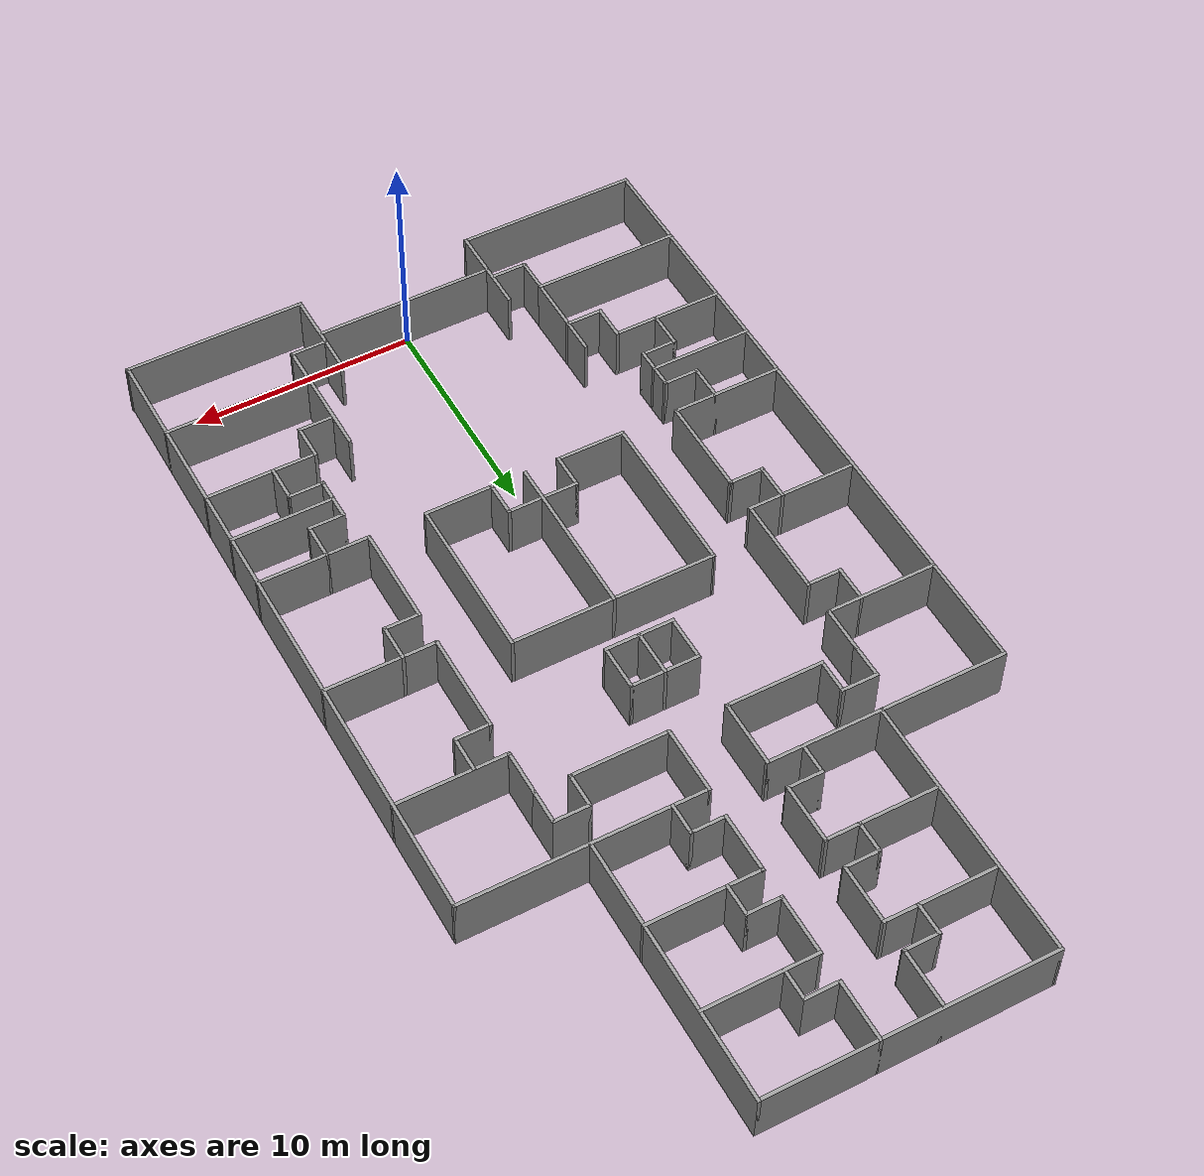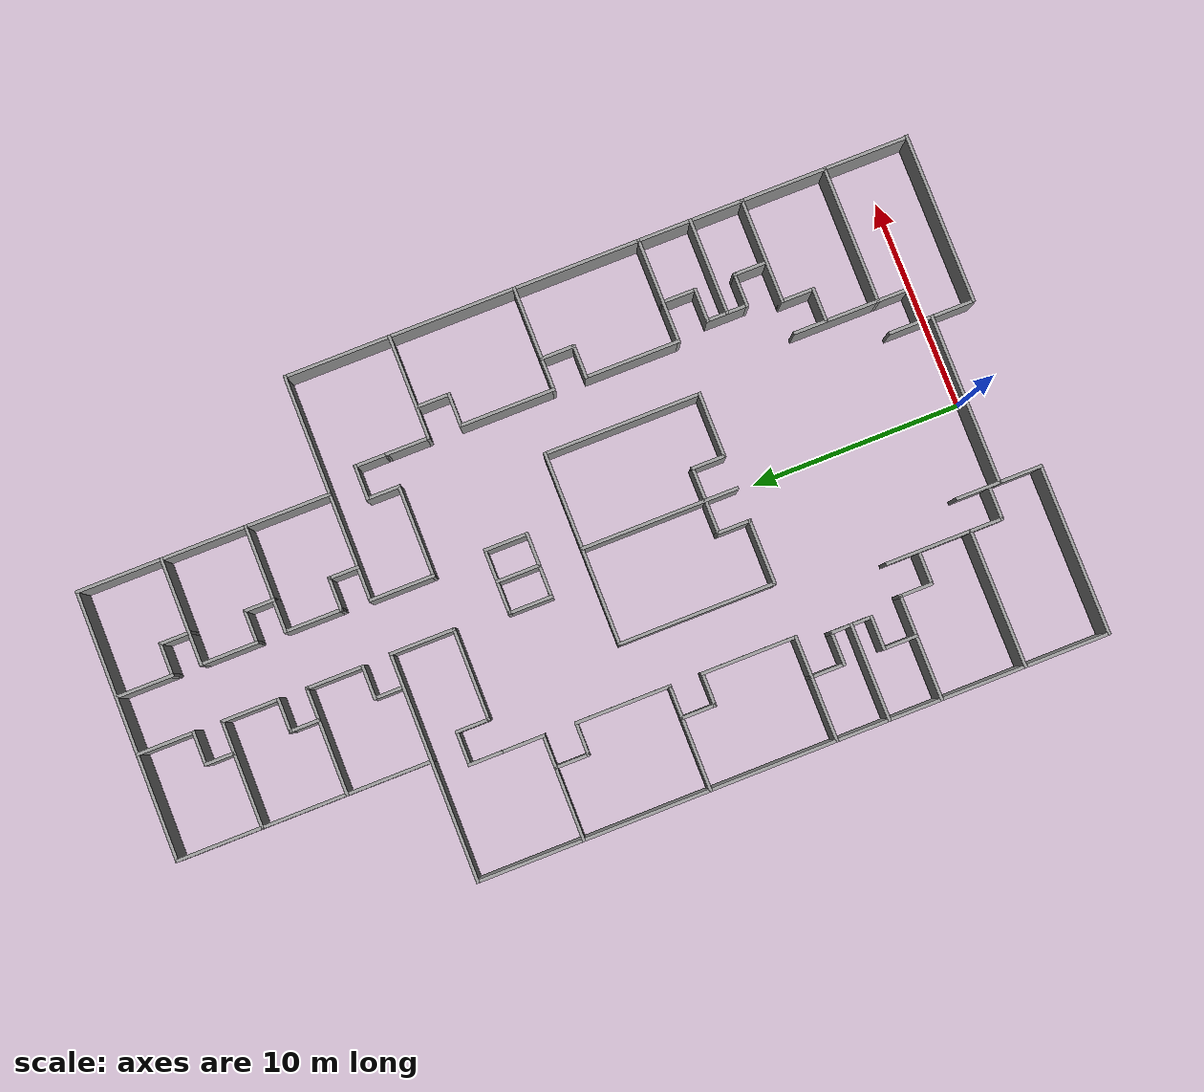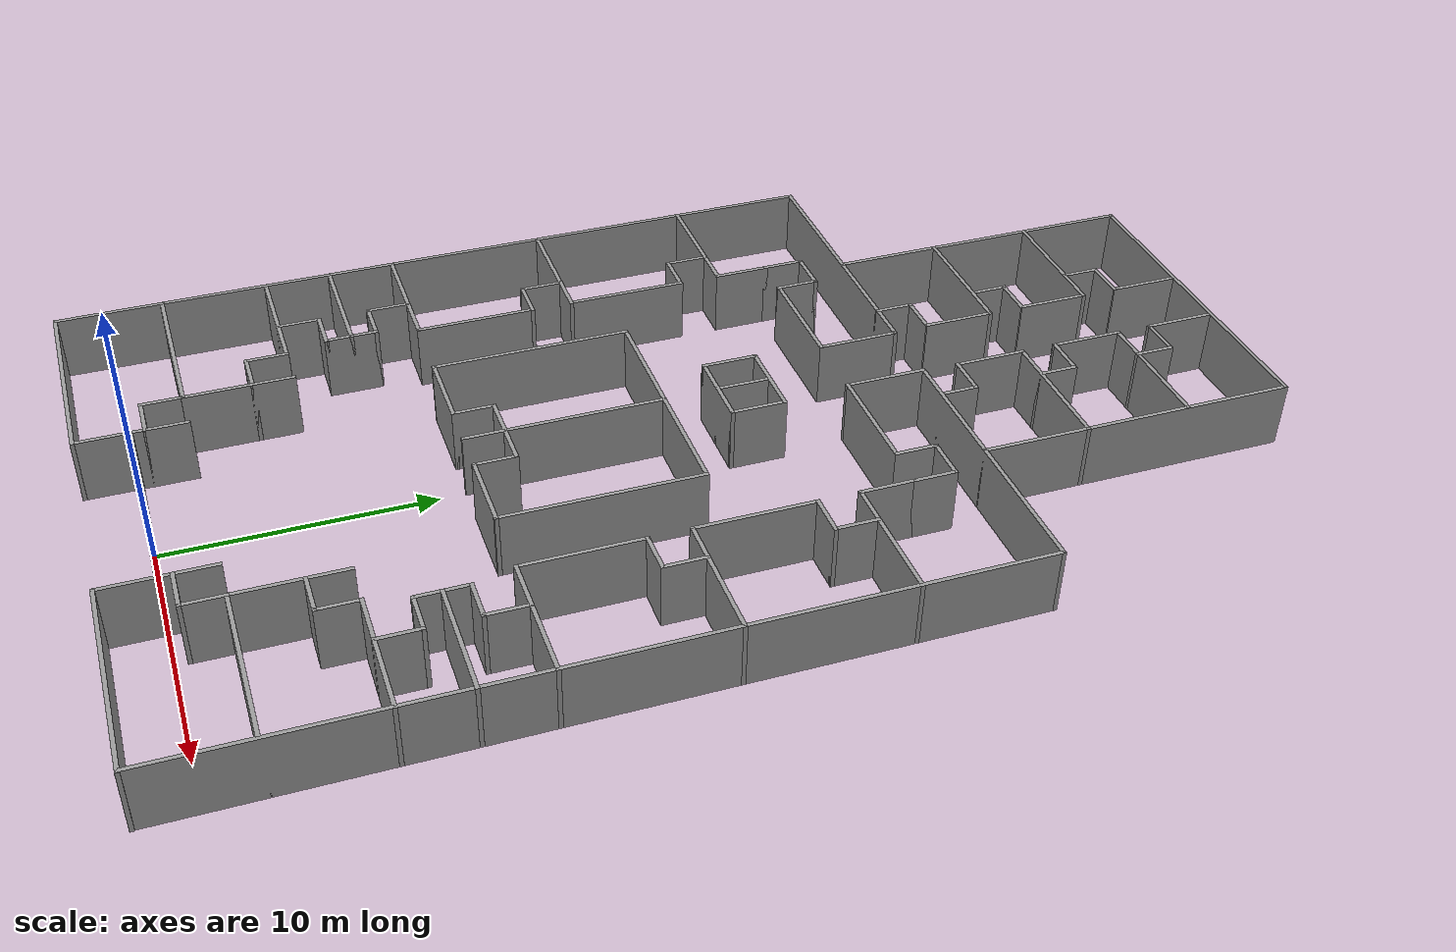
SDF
<?xml version='1.0'?>
<sdf version='1.6'>
  <model name='hospital__restricted_model'>
    <pose frame=''>0.015862 19 0 0 -0 0</pose>
    <link name='Wall_0'>
      <collision name='Wall_0_Collision'>
        <geometry>
          <box>
            <size>4.15 0.15 2.5</size>
          </box>
        </geometry>
        <pose frame=''>0 0 1.25 0 -0 0</pose>
      </collision>
      <visual name='Wall_0_Visual'>
        <pose frame=''>0 0 1.25 0 -0 0</pose>
        <geometry>
          <box>
            <size>4.15 0.15 2.5</size>
          </box>
        </geometry>
        <material>
          <script>
            <uri>file://media/materials/scripts/gazebo.material</uri>
            <name>Gazebo/Grey</name>
          </script>
          <ambient>1 1 1 1</ambient>
        </material>
        <meta>
          <layer>0</layer>
        </meta>
      </visual>
      <pose frame=''>-4.01586 -19 0 0 -0 -1.5708</pose>
    </link>
    <link name='Wall_10'>
      <collision name='Wall_10_Collision'>
        <geometry>
          <box>
            <size>6.6 0.15 2.5</size>
          </box>
        </geometry>
        <pose frame=''>0 0 1.25 0 -0 0</pose>
      </collision>
      <visual name='Wall_10_Visual'>
        <pose frame=''>0 0 1.25 0 -0 0</pose>
        <geometry>
          <box>
            <size>6.6 0.15 2.5</size>
          </box>
        </geometry>
        <material>
          <script>
            <uri>file://media/materials/scripts/gazebo.material</uri>
            <name>Gazebo/Grey</name>
          </script>
          <ambient>1 1 1 1</ambient>
        </material>
        <meta>
          <layer>0</layer>
        </meta>
      </visual>
      <pose frame=''>-8.79086 -17 0 0 -0 3.14159</pose>
    </link>
    <link name='Wall_100'>
      <collision name='Wall_100_Collision'>
        <geometry>
          <box>
            <size>2.8 0.15 2.5</size>
          </box>
        </geometry>
        <pose frame=''>0 0 1.25 0 -0 0</pose>
      </collision>
      <visual name='Wall_100_Visual'>
        <pose frame=''>0 0 1.25 0 -0 0</pose>
        <geometry>
          <box>
            <size>2.8 0.15 2.5</size>
          </box>
        </geometry>
        <material>
          <script>
            <uri>file://media/materials/scripts/gazebo.material</uri>
            <name>Gazebo/Grey</name>
          </script>
          <ambient>1 1 1 1</ambient>
        </material>
        <meta>
          <layer>0</layer>
        </meta>
      </visual>
      <pose frame=''>1.33414 19.675 0 0 -0 1.5708</pose>
    </link>
    <link name='Wall_102'>
      <collision name='Wall_102_Collision'>
        <geometry>
          <box>
            <size>3.15 0.15 2.5</size>
          </box>
        </geometry>
        <pose frame=''>0 0 1.25 0 -0 0</pose>
      </collision>
      <visual name='Wall_102_Visual'>
        <pose frame=''>0 0 1.25 0 -0 0</pose>
        <geometry>
          <box>
            <size>3.15 0.15 2.5</size>
          </box>
        </geometry>
        <material>
          <script>
            <uri>file://media/materials/scripts/gazebo.material</uri>
            <name>Gazebo/Grey</name>
          </script>
          <ambient>1 1 1 1</ambient>
        </material>
        <meta>
          <layer>0</layer>
        </meta>
      </visual>
      <pose frame=''>-3.06586 -8 0 0 -0 0</pose>
    </link>
    <link name='Wall_104'>
      <collision name='Wall_104_Collision'>
        <geometry>
          <box>
            <size>3.15 0.15 2.5</size>
          </box>
        </geometry>
        <pose frame=''>0 0 1.25 0 -0 0</pose>
      </collision>
      <visual name='Wall_104_Visual'>
        <pose frame=''>0 0 1.25 0 -0 0</pose>
        <geometry>
          <box>
            <size>3.15 0.15 2.5</size>
          </box>
        </geometry>
        <material>
          <script>
            <uri>file://media/materials/scripts/gazebo.material</uri>
            <name>Gazebo/Grey</name>
          </script>
          <ambient>1 1 1 1</ambient>
        </material>
        <meta>
          <layer>0</layer>
        </meta>
      </visual>
      <pose frame=''>3.03414 -8 0 0 -0 0</pose>
    </link>
    <link name='Wall_106'>
      <collision name='Wall_106_Collision'>
        <geometry>
          <box>
            <size>7.55 0.15 2.5</size>
          </box>
        </geometry>
        <pose frame=''>0 0 1.25 0 -0 0</pose>
      </collision>
      <visual name='Wall_106_Visual'>
        <pose frame=''>0 0 1.25 0 -0 0</pose>
        <geometry>
          <box>
            <size>7.55 0.15 2.5</size>
          </box>
        </geometry>
        <material>
          <script>
            <uri>file://media/materials/scripts/gazebo.material</uri>
            <name>Gazebo/Grey</name>
          </script>
          <ambient>1 1 1 1</ambient>
        </material>
        <meta>
          <layer>0</layer>
        </meta>
      </visual>
      <pose frame=''>-4.56386 -4.3 0 0 -0 1.57134</pose>
    </link>
    <link name='Wall_108'>
      <collision name='Wall_108_Collision'>
        <geometry>
          <box>
            <size>9.25 0.15 2.5</size>
          </box>
        </geometry>
        <pose frame=''>0 0 1.25 0 -0 0</pose>
      </collision>
      <visual name='Wall_108_Visual'>
        <pose frame=''>0 0 1.25 0 -0 0</pose>
        <geometry>
          <box>
            <size>9.25 0.15 2.5</size>
          </box>
        </geometry>
        <material>
          <script>
            <uri>file://media/materials/scripts/gazebo.material</uri>
            <name>Gazebo/Grey</name>
          </script>
          <ambient>1 1 1 1</ambient>
        </material>
        <meta>
          <layer>0</layer>
        </meta>
      </visual>
      <pose frame=''>-0.015862 -0.6 0 0 -0 0</pose>
    </link>
    <link name='Wall_110'>
      <collision name='Wall_110_Collision'>
        <geometry>
          <box>
            <size>3.15 0.15 2.5</size>
          </box>
        </geometry>
        <pose frame=''>0 0 1.25 0 -0 0</pose>
      </collision>
      <visual name='Wall_110_Visual'>
        <pose frame=''>0 0 1.25 0 -0 0</pose>
        <geometry>
          <box>
            <size>3.15 0.15 2.5</size>
          </box>
        </geometry>
        <material>
          <script>
            <uri>file://media/materials/scripts/gazebo.material</uri>
            <name>Gazebo/Grey</name>
          </script>
          <ambient>1 1 1 1</ambient>
        </material>
        <meta>
          <layer>0</layer>
        </meta>
      </visual>
      <pose frame=''>-0.015862 3.45 0 0 -0 0</pose>
    </link>
    <link name='Wall_112'>
      <collision name='Wall_112_Collision'>
        <geometry>
          <box>
            <size>3.15 0.15 2.5</size>
          </box>
        </geometry>
        <pose frame=''>0 0 1.25 0 -0 0</pose>
      </collision>
      <visual name='Wall_112_Visual'>
        <pose frame=''>0 0 1.25 0 -0 0</pose>
        <geometry>
          <box>
            <size>3.15 0.15 2.5</size>
          </box>
        </geometry>
        <material>
          <script>
            <uri>file://media/materials/scripts/gazebo.material</uri>
            <name>Gazebo/Grey</name>
          </script>
          <ambient>1 1 1 1</ambient>
        </material>
        <meta>
          <layer>0</layer>
        </meta>
      </visual>
      <pose frame=''>-0.015862 1.45 0 0 -0 0</pose>
    </link>
    <link name='Wall_114'>
      <collision name='Wall_114_Collision'>
        <geometry>
          <box>
            <size>2.15 0.15 2.5</size>
          </box>
        </geometry>
        <pose frame=''>0 0 1.25 0 -0 0</pose>
      </collision>
      <visual name='Wall_114_Visual'>
        <pose frame=''>0 0 1.25 0 -0 0</pose>
        <geometry>
          <box>
            <size>2.15 0.15 2.5</size>
          </box>
        </geometry>
        <material>
          <script>
            <uri>file://media/materials/scripts/gazebo.material</uri>
            <name>Gazebo/Grey</name>
          </script>
          <ambient>1 1 1 1</ambient>
        </material>
        <meta>
          <layer>0</layer>
        </meta>
      </visual>
      <pose frame=''>-1.51586 2.45 0 0 -0 -1.5708</pose>
    </link>
    <link name='Wall_116'>
      <collision name='Wall_116_Collision'>
        <geometry>
          <box>
            <size>2.15 0.15 2.5</size>
          </box>
        </geometry>
        <pose frame=''>0 0 1.25 0 -0 0</pose>
      </collision>
      <visual name='Wall_116_Visual'>
        <pose frame=''>0 0 1.25 0 -0 0</pose>
        <geometry>
          <box>
            <size>2.15 0.15 2.5</size>
          </box>
        </geometry>
        <material>
          <script>
            <uri>file://media/materials/scripts/gazebo.material</uri>
            <name>Gazebo/Grey</name>
          </script>
          <ambient>1 1 1 1</ambient>
        </material>
        <meta>
          <layer>0</layer>
        </meta>
      </visual>
      <pose frame=''>1.48414 2.45 0 0 -0 -1.5708</pose>
    </link>
    <link name='Wall_118'>
      <collision name='Wall_118_Collision'>
        <geometry>
          <box>
            <size>2.15 0.15 2.5</size>
          </box>
        </geometry>
        <pose frame=''>0 0 1.25 0 -0 0</pose>
      </collision>
      <visual name='Wall_118_Visual'>
        <pose frame=''>0 0 1.25 0 -0 0</pose>
        <geometry>
          <box>
            <size>2.15 0.15 2.5</size>
          </box>
        </geometry>
        <material>
          <script>
            <uri>file://media/materials/scripts/gazebo.material</uri>
            <name>Gazebo/Grey</name>
          </script>
          <ambient>1 1 1 1</ambient>
        </material>
        <meta>
          <layer>0</layer>
        </meta>
      </visual>
      <pose frame=''>-0.015862 2.45 0 0 -0 -1.5708</pose>
    </link>
    <link name='Wall_12'>
      <collision name='Wall_12_Collision'>
        <geometry>
          <box>
            <size>4.15 0.15 2.5</size>
          </box>
        </geometry>
        <pose frame=''>0 0 1.25 0 -0 0</pose>
      </collision>
      <visual name='Wall_12_Visual'>
        <pose frame=''>0 0 1.25 0 -0 0</pose>
        <geometry>
          <box>
            <size>4.15 0.15 2.5</size>
          </box>
        </geometry>
        <material>
          <script>
            <uri>file://media/materials/scripts/gazebo.material</uri>
            <name>Gazebo/Grey</name>
          </script>
          <ambient>1 1 1 1</ambient>
        </material>
        <meta>
          <layer>0</layer>
        </meta>
      </visual>
      <pose frame=''>-5.56586 -15 0 0 -0 1.5708</pose>
    </link>
    <link name='Wall_121'>
      <collision name='Wall_121_Collision'>
        <geometry>
          <box>
            <size>7.55 0.15 2.5</size>
          </box>
        </geometry>
        <pose frame=''>0 0 1.25 0 -0 0</pose>
      </collision>
      <visual name='Wall_121_Visual'>
        <pose frame=''>0 0 1.25 0 -0 0</pose>
        <geometry>
          <box>
            <size>7.55 0.15 2.5</size>
          </box>
        </geometry>
        <material>
          <script>
            <uri>file://media/materials/scripts/gazebo.material</uri>
            <name>Gazebo/Grey</name>
          </script>
          <ambient>1 1 1 1</ambient>
        </material>
        <meta>
          <layer>0</layer>
        </meta>
      </visual>
      <pose frame=''>4.53414 -4.3 0 0 -0 -1.5708</pose>
    </link>
    <link name='Wall_123'>
      <collision name='Wall_123_Collision'>
        <geometry>
          <box>
            <size>7.55 0.15 2.5</size>
          </box>
        </geometry>
        <pose frame=''>0 0 1.25 0 -0 0</pose>
      </collision>
      <visual name='Wall_123_Visual'>
        <pose frame=''>0 0 1.25 0 -0 0</pose>
        <geometry>
          <box>
            <size>7.55 0.15 2.5</size>
          </box>
        </geometry>
        <material>
          <script>
            <uri>file://media/materials/scripts/gazebo.material</uri>
            <name>Gazebo/Grey</name>
          </script>
          <ambient>1 1 1 1</ambient>
        </material>
        <meta>
          <layer>0</layer>
        </meta>
      </visual>
      <pose frame=''>-0.015862 -4.3 0 0 -0 -1.5708</pose>
    </link>
    <link name='Wall_125'>
      <collision name='Wall_125_Collision'>
        <geometry>
          <box>
            <size>1.65 0.15 2.5</size>
          </box>
        </geometry>
        <pose frame=''>0 0 1.25 0 -0 0</pose>
      </collision>
      <visual name='Wall_125_Visual'>
        <pose frame=''>0 0 1.25 0 -0 0</pose>
        <geometry>
          <box>
            <size>1.65 0.15 2.5</size>
          </box>
        </geometry>
        <material>
          <script>
            <uri>file://media/materials/scripts/gazebo.material</uri>
            <name>Gazebo/Grey</name>
          </script>
          <ambient>1 1 1 1</ambient>
        </material>
        <meta>
          <layer>0</layer>
        </meta>
      </visual>
      <pose frame=''>-5.56586 -17.75 0 0 -0 -1.5708</pose>
    </link>
    <link name='Wall_127'>
      <collision name='Wall_127_Collision'>
        <geometry>
          <box>
            <size>1.7 0.15 2.5</size>
          </box>
        </geometry>
        <pose frame=''>0 0 1.25 0 -0 0</pose>
      </collision>
      <visual name='Wall_127_Visual'>
        <pose frame=''>0 0 1.25 0 -0 0</pose>
        <geometry>
          <box>
            <size>1.7 0.15 2.5</size>
          </box>
        </geometry>
        <material>
          <script>
            <uri>file://media/materials/scripts/gazebo.material</uri>
            <name>Gazebo/Grey</name>
          </script>
          <ambient>1 1 1 1</ambient>
        </material>
        <meta>
          <layer>0</layer>
        </meta>
      </visual>
      <pose frame=''>-4.79086 -18.5 0 0 -0 0</pose>
    </link>
    <link name='Wall_129'>
      <collision name='Wall_129_Collision'>
        <geometry>
          <box>
            <size>1.65 0.15 2.5</size>
          </box>
        </geometry>
        <pose frame=''>0 0 1.25 0 -0 0</pose>
      </collision>
      <visual name='Wall_129_Visual'>
        <pose frame=''>0 0 1.25 0 -0 0</pose>
        <geometry>
          <box>
            <size>1.65 0.15 2.5</size>
          </box>
        </geometry>
        <material>
          <script>
            <uri>file://media/materials/scripts/gazebo.material</uri>
            <name>Gazebo/Grey</name>
          </script>
          <ambient>1 1 1 1</ambient>
        </material>
        <meta>
          <layer>0</layer>
        </meta>
      </visual>
      <pose frame=''>5.53414 -17.75 0 0 -0 -1.5708</pose>
    </link>
    <link name='Wall_131'>
      <collision name='Wall_131_Collision'>
        <geometry>
          <box>
            <size>1.7 0.15 2.5</size>
          </box>
        </geometry>
        <pose frame=''>0 0 1.25 0 -0 0</pose>
      </collision>
      <visual name='Wall_131_Visual'>
        <pose frame=''>0 0 1.25 0 -0 0</pose>
        <geometry>
          <box>
            <size>1.7 0.15 2.5</size>
          </box>
        </geometry>
        <material>
          <script>
            <uri>file://media/materials/scripts/gazebo.material</uri>
            <name>Gazebo/Grey</name>
          </script>
          <ambient>1 1 1 1</ambient>
        </material>
        <meta>
          <layer>0</layer>
        </meta>
      </visual>
      <pose frame=''>4.75914 -18.5 0 0 -0 3.14159</pose>
    </link>
    <link name='Wall_133'>
      <collision name='Wall_133_Collision'>
        <geometry>
          <box>
            <size>1.65 0.15 2.5</size>
          </box>
        </geometry>
        <pose frame=''>0 0 1.25 0 -0 0</pose>
      </collision>
      <visual name='Wall_133_Visual'>
        <pose frame=''>0 0 1.25 0 -0 0</pose>
        <geometry>
          <box>
            <size>1.65 0.15 2.5</size>
          </box>
        </geometry>
        <material>
          <script>
            <uri>file://media/materials/scripts/gazebo.material</uri>
            <name>Gazebo/Grey</name>
          </script>
          <ambient>1 1 1 1</ambient>
        </material>
        <meta>
          <layer>0</layer>
        </meta>
      </visual>
      <pose frame=''>-7.11586 -13.75 0 0 -0 -1.5708</pose>
    </link>
    <link name='Wall_135'>
      <collision name='Wall_135_Collision'>
        <geometry>
          <box>
            <size>1.7 0.15 2.5</size>
          </box>
        </geometry>
        <pose frame=''>0 0 1.25 0 -0 0</pose>
      </collision>
      <visual name='Wall_135_Visual'>
        <pose frame=''>0 0 1.25 0 -0 0</pose>
        <geometry>
          <box>
            <size>1.7 0.15 2.5</size>
          </box>
        </geometry>
        <material>
          <script>
            <uri>file://media/materials/scripts/gazebo.material</uri>
            <name>Gazebo/Grey</name>
          </script>
          <ambient>1 1 1 1</ambient>
        </material>
        <meta>
          <layer>0</layer>
        </meta>
      </visual>
      <pose frame=''>-6.34086 -14.5 0 0 -0 0</pose>
    </link>
    <link name='Wall_137'>
      <collision name='Wall_137_Collision'>
        <geometry>
          <box>
            <size>1.65 0.15 2.5</size>
          </box>
        </geometry>
        <pose frame=''>0 0 1.25 0 -0 0</pose>
      </collision>
      <visual name='Wall_137_Visual'>
        <pose frame=''>0 0 1.25 0 -0 0</pose>
        <geometry>
          <box>
            <size>1.65 0.15 2.5</size>
          </box>
        </geometry>
        <material>
          <script>
            <uri>file://media/materials/scripts/gazebo.material</uri>
            <name>Gazebo/Grey</name>
          </script>
          <ambient>1 1 1 1</ambient>
        </material>
        <meta>
          <layer>0</layer>
        </meta>
      </visual>
      <pose frame=''>7.08414 -13.75 0 0 -0 1.5708</pose>
    </link>
    <link name='Wall_139'>
      <collision name='Wall_139_Collision'>
        <geometry>
          <box>
            <size>1.7 0.15 2.5</size>
          </box>
        </geometry>
        <pose frame=''>0 0 1.25 0 -0 0</pose>
      </collision>
      <visual name='Wall_139_Visual'>
        <pose frame=''>0 0 1.25 0 -0 0</pose>
        <geometry>
          <box>
            <size>1.7 0.15 2.5</size>
          </box>
        </geometry>
        <material>
          <script>
            <uri>file://media/materials/scripts/gazebo.material</uri>
            <name>Gazebo/Grey</name>
          </script>
          <ambient>1 1 1 1</ambient>
        </material>
        <meta>
          <layer>0</layer>
        </meta>
      </visual>
      <pose frame=''>6.30914 -14.5 0 0 -0 3.14159</pose>
    </link>
    <link name='Wall_14'>
      <collision name='Wall_14_Collision'>
        <geometry>
          <box>
            <size>5.05 0.15 2.5</size>
          </box>
        </geometry>
        <pose frame=''>0 0 1.25 0 -0 0</pose>
      </collision>
      <visual name='Wall_14_Visual'>
        <pose frame=''>0 0 1.25 0 -0 0</pose>
        <geometry>
          <box>
            <size>5.05 0.15 2.5</size>
          </box>
        </geometry>
        <material>
          <script>
            <uri>file://media/materials/scripts/gazebo.material</uri>
            <name>Gazebo/Grey</name>
          </script>
          <ambient>1 1 1 1</ambient>
        </material>
        <meta>
          <layer>0</layer>
        </meta>
      </visual>
      <pose frame=''>-9.56586 -13 0 0 -0 3.14159</pose>
    </link>
    <link name='Wall_141'>
      <collision name='Wall_141_Collision'>
        <geometry>
          <box>
            <size>1.65 0.15 2.5</size>
          </box>
        </geometry>
        <pose frame=''>0 0 1.25 0 -0 0</pose>
      </collision>
      <visual name='Wall_141_Visual'>
        <pose frame=''>0 0 1.25 0 -0 0</pose>
        <geometry>
          <box>
            <size>1.65 0.15 2.5</size>
          </box>
        </geometry>
        <material>
          <script>
            <uri>file://media/materials/scripts/gazebo.material</uri>
            <name>Gazebo/Grey</name>
          </script>
          <ambient>1 1 1 1</ambient>
        </material>
        <meta>
          <layer>0</layer>
        </meta>
      </visual>
      <pose frame=''>-8.26586 -11.45 0 0 -0 3.14159</pose>
    </link>
    <link name='Wall_143'>
      <collision name='Wall_143_Collision'>
        <geometry>
          <box>
            <size>1.7 0.15 2.5</size>
          </box>
        </geometry>
        <pose frame=''>0 0 1.25 0 -0 0</pose>
      </collision>
      <visual name='Wall_143_Visual'>
        <pose frame=''>0 0 1.25 0 -0 0</pose>
        <geometry>
          <box>
            <size>1.7 0.15 2.5</size>
          </box>
        </geometry>
        <material>
          <script>
            <uri>file://media/materials/scripts/gazebo.material</uri>
            <name>Gazebo/Grey</name>
          </script>
          <ambient>1 1 1 1</ambient>
        </material>
        <meta>
          <layer>0</layer>
        </meta>
      </visual>
      <pose frame=''>-9.01586 -12.225 0 0 -0 -1.5708</pose>
    </link>
    <link name='Wall_145'>
      <collision name='Wall_145_Collision'>
        <geometry>
          <box>
            <size>1.65 0.15 2.5</size>
          </box>
        </geometry>
        <pose frame=''>0 0 1.25 0 -0 0</pose>
      </collision>
      <visual name='Wall_145_Visual'>
        <pose frame=''>0 0 1.25 0 -0 0</pose>
        <geometry>
          <box>
            <size>1.65 0.15 2.5</size>
          </box>
        </geometry>
        <material>
          <script>
            <uri>file://media/materials/scripts/gazebo.material</uri>
            <name>Gazebo/Grey</name>
          </script>
          <ambient>1 1 1 1</ambient>
        </material>
        <meta>
          <layer>0</layer>
        </meta>
      </visual>
      <pose frame=''>-8.26586 -9.55 0 0 -0 3.14159</pose>
    </link>
    <link name='Wall_147'>
      <collision name='Wall_147_Collision'>
        <geometry>
          <box>
            <size>1.7 0.15 2.5</size>
          </box>
        </geometry>
        <pose frame=''>0 0 1.25 0 -0 0</pose>
      </collision>
      <visual name='Wall_147_Visual'>
        <pose frame=''>0 0 1.25 0 -0 0</pose>
        <geometry>
          <box>
            <size>1.7 0.15 2.5</size>
          </box>
        </geometry>
        <material>
          <script>
            <uri>file://media/materials/scripts/gazebo.material</uri>
            <name>Gazebo/Grey</name>
          </script>
          <ambient>1 1 1 1</ambient>
        </material>
        <meta>
          <layer>0</layer>
        </meta>
      </visual>
      <pose frame=''>-9.01586 -8.775 0 0 -0 -1.5708</pose>
    </link>
    <link name='Wall_149'>
      <collision name='Wall_149_Collision'>
        <geometry>
          <box>
            <size>1.65 0.15 2.5</size>
          </box>
        </geometry>
        <pose frame=''>0 0 1.25 0 -0 0</pose>
      </collision>
      <visual name='Wall_149_Visual'>
        <pose frame=''>0 0 1.25 0 -0 0</pose>
        <geometry>
          <box>
            <size>1.65 0.15 2.5</size>
          </box>
        </geometry>
        <material>
          <script>
            <uri>file://media/materials/scripts/gazebo.material</uri>
            <name>Gazebo/Grey</name>
          </script>
          <ambient>1 1 1 1</ambient>
        </material>
        <meta>
          <layer>0</layer>
        </meta>
      </visual>
      <pose frame=''>-7.86586 -3.55 0 0 -0 0</pose>
    </link>
    <link name='Wall_151'>
      <collision name='Wall_151_Collision'>
        <geometry>
          <box>
            <size>1.7 0.15 2.5</size>
          </box>
        </geometry>
        <pose frame=''>0 0 1.25 0 -0 0</pose>
      </collision>
      <visual name='Wall_151_Visual'>
        <pose frame=''>0 0 1.25 0 -0 0</pose>
        <geometry>
          <box>
            <size>1.7 0.15 2.5</size>
          </box>
        </geometry>
        <material>
          <script>
            <uri>file://media/materials/scripts/gazebo.material</uri>
            <name>Gazebo/Grey</name>
          </script>
          <ambient>1 1 1 1</ambient>
        </material>
        <meta>
          <layer>0</layer>
        </meta>
      </visual>
      <pose frame=''>-8.61586 -2.775 0 0 -0 1.5708</pose>
    </link>
    <link name='Wall_153'>
      <collision name='Wall_153_Collision'>
        <geometry>
          <box>
            <size>1.7 0.15 2.5</size>
          </box>
        </geometry>
        <pose frame=''>0 0 1.25 0 -0 0</pose>
      </collision>
      <visual name='Wall_153_Visual'>
        <pose frame=''>0 0 1.25 0 -0 0</pose>
        <geometry>
          <box>
            <size>1.7 0.15 2.5</size>
          </box>
        </geometry>
        <material>
          <script>
            <uri>file://media/materials/scripts/gazebo.material</uri>
            <name>Gazebo/Grey</name>
          </script>
          <ambient>1 1 1 1</ambient>
        </material>
        <meta>
          <layer>0</layer>
        </meta>
      </visual>
      <pose frame=''>-8.61586 3.225 0 0 -0 1.5708</pose>
    </link>
    <link name='Wall_155'>
      <collision name='Wall_155_Collision'>
        <geometry>
          <box>
            <size>1.65 0.15 2.5</size>
          </box>
        </geometry>
        <pose frame=''>0 0 1.25 0 -0 0</pose>
      </collision>
      <visual name='Wall_155_Visual'>
        <pose frame=''>0 0 1.25 0 -0 0</pose>
        <geometry>
          <box>
            <size>1.65 0.15 2.5</size>
          </box>
        </geometry>
        <material>
          <script>
            <uri>file://media/materials/scripts/gazebo.material</uri>
            <name>Gazebo/Grey</name>
          </script>
          <ambient>1 1 1 1</ambient>
        </material>
        <meta>
          <layer>0</layer>
        </meta>
      </visual>
      <pose frame=''>-7.86586 2.45 0 0 -0 0</pose>
    </link>
    <link name='Wall_157'>
      <collision name='Wall_157_Collision'>
        <geometry>
          <box>
            <size>1.65 0.15 2.5</size>
          </box>
        </geometry>
        <pose frame=''>0 0 1.25 0 -0 0</pose>
      </collision>
      <visual name='Wall_157_Visual'>
        <pose frame=''>0 0 1.25 0 -0 0</pose>
        <geometry>
          <box>
            <size>1.65 0.15 2.5</size>
          </box>
        </geometry>
        <material>
          <script>
            <uri>file://media/materials/scripts/gazebo.material</uri>
            <name>Gazebo/Grey</name>
          </script>
          <ambient>1 1 1 1</ambient>
        </material>
        <meta>
          <layer>0</layer>
        </meta>
      </visual>
      <pose frame=''>-5.56586 6.75 0 0 -0 1.5708</pose>
    </link>
    <link name='Wall_159'>
      <collision name='Wall_159_Collision'>
        <geometry>
          <box>
            <size>1.7 0.15 2.5</size>
          </box>
        </geometry>
        <pose frame=''>0 0 1.25 0 -0 0</pose>
      </collision>
      <visual name='Wall_159_Visual'>
        <pose frame=''>0 0 1.25 0 -0 0</pose>
        <geometry>
          <box>
            <size>1.7 0.15 2.5</size>
          </box>
        </geometry>
        <material>
          <script>
            <uri>file://media/materials/scripts/gazebo.material</uri>
            <name>Gazebo/Grey</name>
          </script>
          <ambient>1 1 1 1</ambient>
        </material>
        <meta>
          <layer>0</layer>
        </meta>
      </visual>
      <pose frame=''>-6.34086 7.5 0 0 -0 3.14159</pose>
    </link>
    <link name='Wall_161'>
      <collision name='Wall_161_Collision'>
        <geometry>
          <box>
            <size>1.65 0.15 2.5</size>
          </box>
        </geometry>
        <pose frame=''>0 0 1.25 0 -0 0</pose>
      </collision>
      <visual name='Wall_161_Visual'>
        <pose frame=''>0 0 1.25 0 -0 0</pose>
        <geometry>
          <box>
            <size>1.65 0.15 2.5</size>
          </box>
        </geometry>
        <material>
          <script>
            <uri>file://media/materials/scripts/gazebo.material</uri>
            <name>Gazebo/Grey</name>
          </script>
          <ambient>1 1 1 1</ambient>
        </material>
        <meta>
          <layer>0</layer>
        </meta>
      </visual>
      <pose frame=''>-7.11586 6.75 0 0 -0 -1.5708</pose>
    </link>
    <link name='Wall_163'>
      <collision name='Wall_163_Collision'>
        <geometry>
          <box>
            <size>1.5 0.15 2.5</size>
          </box>
        </geometry>
        <pose frame=''>0 0 1.25 0 -0 0</pose>
      </collision>
      <visual name='Wall_163_Visual'>
        <pose frame=''>0 0 1.25 0 -0 0</pose>
        <geometry>
          <box>
            <size>1.5 0.15 2.5</size>
          </box>
        </geometry>
        <material>
          <script>
            <uri>file://media/materials/scripts/gazebo.material</uri>
            <name>Gazebo/Grey</name>
          </script>
          <ambient>1 1 1 1</ambient>
        </material>
        <meta>
          <layer>0</layer>
        </meta>
      </visual>
      <pose frame=''>-2.86586 9.675 0 0 -0 1.5708</pose>
    </link>
    <link name='Wall_168'>
      <collision name='Wall_168_Collision'>
        <geometry>
          <box>
            <size>1.65 0.15 2.5</size>
          </box>
        </geometry>
        <pose frame=''>0 0 1.25 0 -0 0</pose>
      </collision>
      <visual name='Wall_168_Visual'>
        <pose frame=''>0 0 1.25 0 -0 0</pose>
        <geometry>
          <box>
            <size>1.65 0.15 2.5</size>
          </box>
        </geometry>
        <material>
          <script>
            <uri>file://media/materials/scripts/gazebo.material</uri>
            <name>Gazebo/Grey</name>
          </script>
          <ambient>1 1 1 1</ambient>
        </material>
        <meta>
          <layer>0</layer>
        </meta>
      </visual>
      <pose frame=''>-2.11586 10.35 0 0 -0 0</pose>
    </link>
    <link name='Wall_17'>
      <collision name='Wall_17_Collision'>
        <geometry>
          <box>
            <size>2.05 0.15 2.5</size>
          </box>
        </geometry>
        <pose frame=''>0 0 1.25 0 -0 0</pose>
      </collision>
      <visual name='Wall_17_Visual'>
        <pose frame=''>0 0 1.25 0 -0 0</pose>
        <geometry>
          <box>
            <size>2.05 0.15 2.5</size>
          </box>
        </geometry>
        <material>
          <script>
            <uri>file://media/materials/scripts/gazebo.material</uri>
            <name>Gazebo/Grey</name>
          </script>
          <ambient>1 1 1 1</ambient>
        </material>
        <meta>
          <layer>0</layer>
        </meta>
      </visual>
      <pose frame=''>-7.51586 -10.5 0 0 -0 1.5708</pose>
    </link>
    <link name='Wall_170'>
      <collision name='Wall_170_Collision'>
        <geometry>
          <box>
            <size>1.65 0.15 2.5</size>
          </box>
        </geometry>
        <pose frame=''>0 0 1.25 0 -0 0</pose>
      </collision>
      <visual name='Wall_170_Visual'>
        <pose frame=''>0 0 1.25 0 -0 0</pose>
        <geometry>
          <box>
            <size>1.65 0.15 2.5</size>
          </box>
        </geometry>
        <material>
          <script>
            <uri>file://media/materials/scripts/gazebo.material</uri>
            <name>Gazebo/Grey</name>
          </script>
          <ambient>1 1 1 1</ambient>
        </material>
        <meta>
          <layer>0</layer>
        </meta>
      </visual>
      <pose frame=''>2.08414 10.35 0 0 -0 0</pose>
    </link>
    <link name='Wall_172'>
      <collision name='Wall_172_Collision'>
        <geometry>
          <box>
            <size>1.5 0.15 2.5</size>
          </box>
        </geometry>
        <pose frame=''>0 0 1.25 0 -0 0</pose>
      </collision>
      <visual name='Wall_172_Visual'>
        <pose frame=''>0 0 1.25 0 -0 0</pose>
        <geometry>
          <box>
            <size>1.5 0.15 2.5</size>
          </box>
        </geometry>
        <material>
          <script>
            <uri>file://media/materials/scripts/gazebo.material</uri>
            <name>Gazebo/Grey</name>
          </script>
          <ambient>1 1 1 1</ambient>
        </material>
        <meta>
          <layer>0</layer>
        </meta>
      </visual>
      <pose frame=''>2.83414 9.675 0 0 -0 -1.5708</pose>
    </link>
    <link name='Wall_174'>
      <collision name='Wall_174_Collision'>
        <geometry>
          <box>
            <size>1.5 0.15 2.5</size>
          </box>
        </geometry>
        <pose frame=''>0 0 1.25 0 -0 0</pose>
      </collision>
      <visual name='Wall_174_Visual'>
        <pose frame=''>0 0 1.25 0 -0 0</pose>
        <geometry>
          <box>
            <size>1.5 0.15 2.5</size>
          </box>
        </geometry>
        <material>
          <script>
            <uri>file://media/materials/scripts/gazebo.material</uri>
            <name>Gazebo/Grey</name>
          </script>
          <ambient>1 1 1 1</ambient>
        </material>
        <meta>
          <layer>0</layer>
        </meta>
      </visual>
      <pose frame=''>-2.86586 13.675 0 0 -0 -1.5708</pose>
    </link>
    <link name='Wall_176'>
      <collision name='Wall_176_Collision'>
        <geometry>
          <box>
            <size>1.65 0.15 2.5</size>
          </box>
        </geometry>
        <pose frame=''>0 0 1.25 0 -0 0</pose>
      </collision>
      <visual name='Wall_176_Visual'>
        <pose frame=''>0 0 1.25 0 -0 0</pose>
        <geometry>
          <box>
            <size>1.65 0.15 2.5</size>
          </box>
        </geometry>
        <material>
          <script>
            <uri>file://media/materials/scripts/gazebo.material</uri>
            <name>Gazebo/Grey</name>
          </script>
          <ambient>1 1 1 1</ambient>
        </material>
        <meta>
          <layer>0</layer>
        </meta>
      </visual>
      <pose frame=''>-2.11586 14.35 0 0 -0 0</pose>
    </link>
    <link name='Wall_178'>
      <collision name='Wall_178_Collision'>
        <geometry>
          <box>
            <size>1.5 0.15 2.5</size>
          </box>
        </geometry>
        <pose frame=''>0 0 1.25 0 -0 0</pose>
      </collision>
      <visual name='Wall_178_Visual'>
        <pose frame=''>0 0 1.25 0 -0 0</pose>
        <geometry>
          <box>
            <size>1.5 0.15 2.5</size>
          </box>
        </geometry>
        <material>
          <script>
            <uri>file://media/materials/scripts/gazebo.material</uri>
            <name>Gazebo/Grey</name>
          </script>
          <ambient>1 1 1 1</ambient>
        </material>
        <meta>
          <layer>0</layer>
        </meta>
      </visual>
      <pose frame=''>-2.86586 17.675 0 0 -0 1.5708</pose>
    </link>
    <link name='Wall_180'>
      <collision name='Wall_180_Collision'>
        <geometry>
          <box>
            <size>1.65 0.15 2.5</size>
          </box>
        </geometry>
        <pose frame=''>0 0 1.25 0 -0 0</pose>
      </collision>
      <visual name='Wall_180_Visual'>
        <pose frame=''>0 0 1.25 0 -0 0</pose>
        <geometry>
          <box>
            <size>1.65 0.15 2.5</size>
          </box>
        </geometry>
        <material>
          <script>
            <uri>file://media/materials/scripts/gazebo.material</uri>
            <name>Gazebo/Grey</name>
          </script>
          <ambient>1 1 1 1</ambient>
        </material>
        <meta>
          <layer>0</layer>
        </meta>
      </visual>
      <pose frame=''>-2.11586 18.35 0 0 -0 0</pose>
    </link>
    <link name='Wall_183'>
      <collision name='Wall_183_Collision'>
        <geometry>
          <box>
            <size>1.65 0.15 2.5</size>
          </box>
        </geometry>
        <pose frame=''>0 0 1.25 0 -0 0</pose>
      </collision>
      <visual name='Wall_183_Visual'>
        <pose frame=''>0 0 1.25 0 -0 0</pose>
        <geometry>
          <box>
            <size>1.65 0.15 2.5</size>
          </box>
        </geometry>
        <material>
          <script>
            <uri>file://media/materials/scripts/gazebo.material</uri>
            <name>Gazebo/Grey</name>
          </script>
          <ambient>1 1 1 1</ambient>
        </material>
        <meta>
          <layer>0</layer>
        </meta>
      </visual>
      <pose frame=''>2.08414 14.35 0 0 -0 0</pose>
    </link>
    <link name='Wall_185'>
      <collision name='Wall_185_Collision'>
        <geometry>
          <box>
            <size>1.5 0.15 2.5</size>
          </box>
        </geometry>
        <pose frame=''>0 0 1.25 0 -0 0</pose>
      </collision>
      <visual name='Wall_185_Visual'>
        <pose frame=''>0 0 1.25 0 -0 0</pose>
        <geometry>
          <box>
            <size>1.5 0.15 2.5</size>
          </box>
        </geometry>
        <material>
          <script>
            <uri>file://media/materials/scripts/gazebo.material</uri>
            <name>Gazebo/Grey</name>
          </script>
          <ambient>1 1 1 1</ambient>
        </material>
        <meta>
          <layer>0</layer>
        </meta>
      </visual>
      <pose frame=''>2.83414 13.675 0 0 -0 -1.5708</pose>
    </link>
    <link name='Wall_187'>
      <collision name='Wall_187_Collision'>
        <geometry>
          <box>
            <size>1.65 0.15 2.5</size>
          </box>
        </geometry>
        <pose frame=''>0 0 1.25 0 -0 0</pose>
      </collision>
      <visual name='Wall_187_Visual'>
        <pose frame=''>0 0 1.25 0 -0 0</pose>
        <geometry>
          <box>
            <size>1.65 0.15 2.5</size>
          </box>
        </geometry>
        <material>
          <script>
            <uri>file://media/materials/scripts/gazebo.material</uri>
            <name>Gazebo/Grey</name>
          </script>
          <ambient>1 1 1 1</ambient>
        </material>
        <meta>
          <layer>0</layer>
        </meta>
      </visual>
      <pose frame=''>2.08414 18.35 0 0 -0 0</pose>
    </link>
    <link name='Wall_189'>
      <collision name='Wall_189_Collision'>
        <geometry>
          <box>
            <size>1.5 0.15 2.5</size>
          </box>
        </geometry>
        <pose frame=''>0 0 1.25 0 -0 0</pose>
      </collision>
      <visual name='Wall_189_Visual'>
        <pose frame=''>0 0 1.25 0 -0 0</pose>
        <geometry>
          <box>
            <size>1.5 0.15 2.5</size>
          </box>
        </geometry>
        <material>
          <script>
            <uri>file://media/materials/scripts/gazebo.material</uri>
            <name>Gazebo/Grey</name>
          </script>
          <ambient>1 1 1 1</ambient>
        </material>
        <meta>
          <layer>0</layer>
        </meta>
      </visual>
      <pose frame=''>2.83414 17.675 0 0 -0 -1.5708</pose>
    </link>
    <link name='Wall_19'>
      <collision name='Wall_19_Collision'>
        <geometry>
          <box>
            <size>4.65 0.15 2.5</size>
          </box>
        </geometry>
        <pose frame=''>0 0 1.25 0 -0 0</pose>
      </collision>
      <visual name='Wall_19_Visual'>
        <pose frame=''>0 0 1.25 0 -0 0</pose>
        <geometry>
          <box>
            <size>4.65 0.15 2.5</size>
          </box>
        </geometry>
        <material>
          <script>
            <uri>file://media/materials/scripts/gazebo.material</uri>
            <name>Gazebo/Grey</name>
          </script>
          <ambient>1 1 1 1</ambient>
        </material>
        <meta>
          <layer>0</layer>
        </meta>
      </visual>
      <pose frame=''>-9.76586 -10.5 0 0 -0 3.14159</pose>
    </link>
    <link name='Wall_192'>
      <collision name='Wall_192_Collision'>
        <geometry>
          <box>
            <size>1.65 0.15 2.5</size>
          </box>
        </geometry>
        <pose frame=''>0 0 1.25 0 -0 0</pose>
      </collision>
      <visual name='Wall_192_Visual'>
        <pose frame=''>0 0 1.25 0 -0 0</pose>
        <geometry>
          <box>
            <size>1.65 0.15 2.5</size>
          </box>
        </geometry>
        <material>
          <script>
            <uri>file://media/materials/scripts/gazebo.material</uri>
            <name>Gazebo/Grey</name>
          </script>
          <ambient>1 1 1 1</ambient>
        </material>
        <meta>
          <layer>0</layer>
        </meta>
      </visual>
      <pose frame=''>5.53414 6.75 0 0 -0 1.5708</pose>
    </link>
    <link name='Wall_194'>
      <collision name='Wall_194_Collision'>
        <geometry>
          <box>
            <size>1.7 0.15 2.5</size>
          </box>
        </geometry>
        <pose frame=''>0 0 1.25 0 -0 0</pose>
      </collision>
      <visual name='Wall_194_Visual'>
        <pose frame=''>0 0 1.25 0 -0 0</pose>
        <geometry>
          <box>
            <size>1.7 0.15 2.5</size>
          </box>
        </geometry>
        <material>
          <script>
            <uri>file://media/materials/scripts/gazebo.material</uri>
            <name>Gazebo/Grey</name>
          </script>
          <ambient>1 1 1 1</ambient>
        </material>
        <meta>
          <layer>0</layer>
        </meta>
      </visual>
      <pose frame=''>6.30914 7.5 0 0 -0 0</pose>
    </link>
    <link name='Wall_196'>
      <collision name='Wall_196_Collision'>
        <geometry>
          <box>
            <size>1.65 0.15 2.5</size>
          </box>
        </geometry>
        <pose frame=''>0 0 1.25 0 -0 0</pose>
      </collision>
      <visual name='Wall_196_Visual'>
        <pose frame=''>0 0 1.25 0 -0 0</pose>
        <geometry>
          <box>
            <size>1.65 0.15 2.5</size>
          </box>
        </geometry>
        <material>
          <script>
            <uri>file://media/materials/scripts/gazebo.material</uri>
            <name>Gazebo/Grey</name>
          </script>
          <ambient>1 1 1 1</ambient>
        </material>
        <meta>
          <layer>0</layer>
        </meta>
      </visual>
      <pose frame=''>7.08414 6.75 0 0 -0 -1.5708</pose>
    </link>
    <link name='Wall_198'>
      <collision name='Wall_198_Collision'>
        <geometry>
          <box>
            <size>1.7 0.15 2.5</size>
          </box>
        </geometry>
        <pose frame=''>0 0 1.25 0 -0 0</pose>
      </collision>
      <visual name='Wall_198_Visual'>
        <pose frame=''>0 0 1.25 0 -0 0</pose>
        <geometry>
          <box>
            <size>1.7 0.15 2.5</size>
          </box>
        </geometry>
        <material>
          <script>
            <uri>file://media/materials/scripts/gazebo.material</uri>
            <name>Gazebo/Grey</name>
          </script>
          <ambient>1 1 1 1</ambient>
        </material>
        <meta>
          <layer>0</layer>
        </meta>
      </visual>
      <pose frame=''>8.58414 3.225 0 0 -0 -1.5708</pose>
    </link>
    <link name='Wall_2'>
      <collision name='Wall_2_Collision'>
        <geometry>
          <box>
            <size>8.15 0.15 2.5</size>
          </box>
        </geometry>
        <pose frame=''>0 0 1.25 0 -0 0</pose>
      </collision>
      <visual name='Wall_2_Visual'>
        <pose frame=''>0 0 1.25 0 -0 0</pose>
        <geometry>
          <box>
            <size>8.15 0.15 2.5</size>
          </box>
        </geometry>
        <material>
          <script>
            <uri>file://media/materials/scripts/gazebo.material</uri>
            <name>Gazebo/Grey</name>
          </script>
          <ambient>1 1 1 1</ambient>
        </material>
        <meta>
          <layer>0</layer>
        </meta>
      </visual>
      <pose frame=''>-0.015862 -19 0 0 -0 0</pose>
    </link>
    <link name='Wall_200'>
      <collision name='Wall_200_Collision'>
        <geometry>
          <box>
            <size>1.65 0.15 2.5</size>
          </box>
        </geometry>
        <pose frame=''>0 0 1.25 0 -0 0</pose>
      </collision>
      <visual name='Wall_200_Visual'>
        <pose frame=''>0 0 1.25 0 -0 0</pose>
        <geometry>
          <box>
            <size>1.65 0.15 2.5</size>
          </box>
        </geometry>
        <material>
          <script>
            <uri>file://media/materials/scripts/gazebo.material</uri>
            <name>Gazebo/Grey</name>
          </script>
          <ambient>1 1 1 1</ambient>
        </material>
        <meta>
          <layer>0</layer>
        </meta>
      </visual>
      <pose frame=''>7.83414 2.45 0 0 -0 3.14159</pose>
    </link>
    <link name='Wall_203'>
      <collision name='Wall_203_Collision'>
        <geometry>
          <box>
            <size>1.7 0.15 2.5</size>
          </box>
        </geometry>
        <pose frame=''>0 0 1.25 0 -0 0</pose>
      </collision>
      <visual name='Wall_203_Visual'>
        <pose frame=''>0 0 1.25 0 -0 0</pose>
        <geometry>
          <box>
            <size>1.7 0.15 2.5</size>
          </box>
        </geometry>
        <material>
          <script>
            <uri>file://media/materials/scripts/gazebo.material</uri>
            <name>Gazebo/Grey</name>
          </script>
          <ambient>1 1 1 1</ambient>
        </material>
        <meta>
          <layer>0</layer>
        </meta>
      </visual>
      <pose frame=''>8.58414 -2.775 0 0 -0 1.5708</pose>
    </link>
    <link name='Wall_205'>
      <collision name='Wall_205_Collision'>
        <geometry>
          <box>
            <size>1.65 0.15 2.5</size>
          </box>
        </geometry>
        <pose frame=''>0 0 1.25 0 -0 0</pose>
      </collision>
      <visual name='Wall_205_Visual'>
        <pose frame=''>0 0 1.25 0 -0 0</pose>
        <geometry>
          <box>
            <size>1.65 0.15 2.5</size>
          </box>
        </geometry>
        <material>
          <script>
            <uri>file://media/materials/scripts/gazebo.material</uri>
            <name>Gazebo/Grey</name>
          </script>
          <ambient>1 1 1 1</ambient>
        </material>
        <meta>
          <layer>0</layer>
        </meta>
      </visual>
      <pose frame=''>7.83414 -3.55 0 0 -0 3.14159</pose>
    </link>
    <link name='Wall_207'>
      <collision name='Wall_207_Collision'>
        <geometry>
          <box>
            <size>1.7 0.15 2.5</size>
          </box>
        </geometry>
        <pose frame=''>0 0 1.25 0 -0 0</pose>
      </collision>
      <visual name='Wall_207_Visual'>
        <pose frame=''>0 0 1.25 0 -0 0</pose>
        <geometry>
          <box>
            <size>1.7 0.15 2.5</size>
          </box>
        </geometry>
        <material>
          <script>
            <uri>file://media/materials/scripts/gazebo.material</uri>
            <name>Gazebo/Grey</name>
          </script>
          <ambient>1 1 1 1</ambient>
        </material>
        <meta>
          <layer>0</layer>
        </meta>
      </visual>
      <pose frame=''>8.98414 -12.225 0 0 -0 1.5708</pose>
    </link>
    <link name='Wall_209'>
      <collision name='Wall_209_Collision'>
        <geometry>
          <box>
            <size>1.65 0.15 2.5</size>
          </box>
        </geometry>
        <pose frame=''>0 0 1.25 0 -0 0</pose>
      </collision>
      <visual name='Wall_209_Visual'>
        <pose frame=''>0 0 1.25 0 -0 0</pose>
        <geometry>
          <box>
            <size>1.65 0.15 2.5</size>
          </box>
        </geometry>
        <material>
          <script>
            <uri>file://media/materials/scripts/gazebo.material</uri>
            <name>Gazebo/Grey</name>
          </script>
          <ambient>1 1 1 1</ambient>
        </material>
        <meta>
          <layer>0</layer>
        </meta>
      </visual>
      <pose frame=''>8.23414 -11.45 0 0 -0 3.14159</pose>
    </link>
    <link name='Wall_21'>
      <collision name='Wall_21_Collision'>
        <geometry>
          <box>
            <size>5.05 0.15 2.5</size>
          </box>
        </geometry>
        <pose frame=''>0 0 1.25 0 -0 0</pose>
      </collision>
      <visual name='Wall_21_Visual'>
        <pose frame=''>0 0 1.25 0 -0 0</pose>
        <geometry>
          <box>
            <size>5.05 0.15 2.5</size>
          </box>
        </geometry>
        <material>
          <script>
            <uri>file://media/materials/scripts/gazebo.material</uri>
            <name>Gazebo/Grey</name>
          </script>
          <ambient>1 1 1 1</ambient>
        </material>
        <meta>
          <layer>0</layer>
        </meta>
      </visual>
      <pose frame=''>-9.56586 -8 0 0 -0 3.14159</pose>
    </link>
    <link name='Wall_211'>
      <collision name='Wall_211_Collision'>
        <geometry>
          <box>
            <size>1.65 0.15 2.5</size>
          </box>
        </geometry>
        <pose frame=''>0 0 1.25 0 -0 0</pose>
      </collision>
      <visual name='Wall_211_Visual'>
        <pose frame=''>0 0 1.25 0 -0 0</pose>
        <geometry>
          <box>
            <size>1.65 0.15 2.5</size>
          </box>
        </geometry>
        <material>
          <script>
            <uri>file://media/materials/scripts/gazebo.material</uri>
            <name>Gazebo/Grey</name>
          </script>
          <ambient>1 1 1 1</ambient>
        </material>
        <meta>
          <layer>0</layer>
        </meta>
      </visual>
      <pose frame=''>8.23414 -9.55 0 0 -0 3.14159</pose>
    </link>
    <link name='Wall_213'>
      <collision name='Wall_213_Collision'>
        <geometry>
          <box>
            <size>1.7 0.15 2.5</size>
          </box>
        </geometry>
        <pose frame=''>0 0 1.25 0 -0 0</pose>
      </collision>
      <visual name='Wall_213_Visual'>
        <pose frame=''>0 0 1.25 0 -0 0</pose>
        <geometry>
          <box>
            <size>1.7 0.15 2.5</size>
          </box>
        </geometry>
        <material>
          <script>
            <uri>file://media/materials/scripts/gazebo.material</uri>
            <name>Gazebo/Grey</name>
          </script>
          <ambient>1 1 1 1</ambient>
        </material>
        <meta>
          <layer>0</layer>
        </meta>
      </visual>
      <pose frame=''>8.98414 -8.775 0 0 -0 -1.5708</pose>
    </link>
    <link name='Wall_215'>
      <collision name='Wall_215_Collision'>
        <geometry>
          <box>
            <size>3.25 0.15 2.5</size>
          </box>
        </geometry>
        <pose frame=''>0 0 1.25 0 -0 0</pose>
      </collision>
      <visual name='Wall_215_Visual'>
        <pose frame=''>0 0 1.25 0 -0 0</pose>
        <geometry>
          <box>
            <size>3.25 0.15 2.5</size>
          </box>
        </geometry>
        <material>
          <script>
            <uri>file://media/materials/scripts/gazebo.material</uri>
            <name>Gazebo/Grey</name>
          </script>
          <ambient>1 1 1 1</ambient>
        </material>
        <meta>
          <layer>0</layer>
        </meta>
      </visual>
      <pose frame=''>-0.015862 -6.5 0 0 -0 0</pose>
    </link>
    <link name='Wall_217'>
      <collision name='Wall_217_Collision'>
        <geometry>
          <box>
            <size>1.65 0.15 2.5</size>
          </box>
        </geometry>
        <pose frame=''>0 0 1.25 0 -0 0</pose>
      </collision>
      <visual name='Wall_217_Visual'>
        <pose frame=''>0 0 1.25 0 -0 0</pose>
        <geometry>
          <box>
            <size>1.65 0.15 2.5</size>
          </box>
        </geometry>
        <material>
          <script>
            <uri>file://media/materials/scripts/gazebo.material</uri>
            <name>Gazebo/Grey</name>
          </script>
          <ambient>1 1 1 1</ambient>
        </material>
        <meta>
          <layer>0</layer>
        </meta>
      </visual>
      <pose frame=''>-1.56586 -7.25 0 0 -0 1.5708</pose>
    </link>
    <link name='Wall_219'>
      <collision name='Wall_219_Collision'>
        <geometry>
          <box>
            <size>1.65 0.15 2.5</size>
          </box>
        </geometry>
        <pose frame=''>0 0 1.25 0 -0 0</pose>
      </collision>
      <visual name='Wall_219_Visual'>
        <pose frame=''>0 0 1.25 0 -0 0</pose>
        <geometry>
          <box>
            <size>1.65 0.15 2.5</size>
          </box>
        </geometry>
        <material>
          <script>
            <uri>file://media/materials/scripts/gazebo.material</uri>
            <name>Gazebo/Grey</name>
          </script>
          <ambient>1 1 1 1</ambient>
        </material>
        <meta>
          <layer>0</layer>
        </meta>
      </visual>
      <pose frame=''>1.53414 -7.25 0 0 -0 -1.5708</pose>
    </link>
    <link name='Wall_23'>
      <collision name='Wall_23_Collision'>
        <geometry>
          <box>
            <size>4.6 0.15 2.5</size>
          </box>
        </geometry>
        <pose frame=''>0 0 1.25 0 -0 0</pose>
      </collision>
      <visual name='Wall_23_Visual'>
        <pose frame=''>0 0 1.25 0 -0 0</pose>
        <geometry>
          <box>
            <size>4.6 0.15 2.5</size>
          </box>
        </geometry>
        <material>
          <script>
            <uri>file://media/materials/scripts/gazebo.material</uri>
            <name>Gazebo/Grey</name>
          </script>
          <ambient>1 1 1 1</ambient>
        </material>
        <meta>
          <layer>0</layer>
        </meta>
      </visual>
      <pose frame=''>-7.11586 -5.775 0 0 -0 1.5708</pose>
    </link>
    <link name='Wall_25'>
      <collision name='Wall_25_Collision'>
        <geometry>
          <box>
            <size>5.05 0.15 2.5</size>
          </box>
        </geometry>
        <pose frame=''>0 0 1.25 0 -0 0</pose>
      </collision>
      <visual name='Wall_25_Visual'>
        <pose frame=''>0 0 1.25 0 -0 0</pose>
        <geometry>
          <box>
            <size>5.05 0.15 2.5</size>
          </box>
        </geometry>
        <material>
          <script>
            <uri>file://media/materials/scripts/gazebo.material</uri>
            <name>Gazebo/Grey</name>
          </script>
          <ambient>1 1 1 1</ambient>
        </material>
        <meta>
          <layer>0</layer>
        </meta>
      </visual>
      <pose frame=''>-9.56586 -2 0 0 -0 3.14159</pose>
    </link>
    <link name='Wall_28'>
      <collision name='Wall_28_Collision'>
        <geometry>
          <box>
            <size>4.6 0.15 2.5</size>
          </box>
        </geometry>
        <pose frame=''>0 0 1.25 0 -0 0</pose>
      </collision>
      <visual name='Wall_28_Visual'>
        <pose frame=''>0 0 1.25 0 -0 0</pose>
        <geometry>
          <box>
            <size>4.6 0.15 2.5</size>
          </box>
        </geometry>
        <material>
          <script>
            <uri>file://media/materials/scripts/gazebo.material</uri>
            <name>Gazebo/Grey</name>
          </script>
          <ambient>1 1 1 1</ambient>
        </material>
        <meta>
          <layer>0</layer>
        </meta>
      </visual>
      <pose frame=''>-7.11586 0.225001 0 0 -0 -1.5708</pose>
    </link>
    <link name='Wall_30'>
      <collision name='Wall_30_Collision'>
        <geometry>
          <box>
            <size>5.05 0.15 2.5</size>
          </box>
        </geometry>
        <pose frame=''>0 0 1.25 0 -0 0</pose>
      </collision>
      <visual name='Wall_30_Visual'>
        <pose frame=''>0 0 1.25 0 -0 0</pose>
        <geometry>
          <box>
            <size>5.05 0.15 2.5</size>
          </box>
        </geometry>
        <material>
          <script>
            <uri>file://media/materials/scripts/gazebo.material</uri>
            <name>Gazebo/Grey</name>
          </script>
          <ambient>1 1 1 1</ambient>
        </material>
        <meta>
          <layer>0</layer>
        </meta>
      </visual>
      <pose frame=''>-9.56586 4 0 0 -0 3.14159</pose>
    </link>
    <link name='Wall_32'>
      <collision name='Wall_32_Collision'>
        <geometry>
          <box>
            <size>2.15 0.15 2.5</size>
          </box>
        </geometry>
        <pose frame=''>0 0 1.25 0 -0 0</pose>
      </collision>
      <visual name='Wall_32_Visual'>
        <pose frame=''>0 0 1.25 0 -0 0</pose>
        <geometry>
          <box>
            <size>2.15 0.15 2.5</size>
          </box>
        </geometry>
        <material>
          <script>
            <uri>file://media/materials/scripts/gazebo.material</uri>
            <name>Gazebo/Grey</name>
          </script>
          <ambient>1 1 1 1</ambient>
        </material>
        <meta>
          <layer>0</layer>
        </meta>
      </visual>
      <pose frame=''>-7.11586 5 0 0 -0 1.5708</pose>
    </link>
    <link name='Wall_34'>
      <collision name='Wall_34_Collision'>
        <geometry>
          <box>
            <size>4.425 0.15 2.5</size>
          </box>
        </geometry>
        <pose frame=''>0 0 1.25 0 -0 0</pose>
      </collision>
      <visual name='Wall_34_Visual'>
        <pose frame=''>0 0 1.25 0 -0 0</pose>
        <geometry>
          <box>
            <size>4.425 0.15 2.5</size>
          </box>
        </geometry>
        <material>
          <script>
            <uri>file://media/materials/scripts/gazebo.material</uri>
            <name>Gazebo/Grey</name>
          </script>
          <ambient>1 1 1 1</ambient>
        </material>
        <meta>
          <layer>0</layer>
        </meta>
      </visual>
      <pose frame=''>-3.42836 6 0 0 -0 0</pose>
    </link>
    <link name='Wall_36'>
      <collision name='Wall_36_Collision'>
        <geometry>
          <box>
            <size>10.875 0.15 2.5</size>
          </box>
        </geometry>
        <pose frame=''>0 0 1.25 0 -0 0</pose>
      </collision>
      <visual name='Wall_36_Visual'>
        <pose frame=''>0 0 1.25 0 -0 0</pose>
        <geometry>
          <box>
            <size>10.875 0.15 2.5</size>
          </box>
        </geometry>
        <material>
          <script>
            <uri>file://media/materials/scripts/gazebo.material</uri>
            <name>Gazebo/Grey</name>
          </script>
          <ambient>1 1 1 1</ambient>
        </material>
        <meta>
          <layer>0</layer>
        </meta>
      </visual>
      <pose frame=''>-6.65336 9 0 0 -0 0</pose>
    </link>
    <link name='Wall_38'>
      <collision name='Wall_38_Collision'>
        <geometry>
          <box>
            <size>2.75 0.15 2.5</size>
          </box>
        </geometry>
        <pose frame=''>0 0 1.25 0 -0 0</pose>
      </collision>
      <visual name='Wall_38_Visual'>
        <pose frame=''>0 0 1.25 0 -0 0</pose>
        <geometry>
          <box>
            <size>2.75 0.15 2.5</size>
          </box>
        </geometry>
        <material>
          <script>
            <uri>file://media/materials/scripts/gazebo.material</uri>
            <name>Gazebo/Grey</name>
          </script>
          <ambient>1 1 1 1</ambient>
        </material>
        <meta>
          <layer>0</layer>
        </meta>
      </visual>
      <pose frame=''>-1.36586 11.7 0 0 -0 1.5708</pose>
    </link>
    <link name='Wall_4'>
      <collision name='Wall_4_Collision'>
        <geometry>
          <box>
            <size>4.15 0.15 2.5</size>
          </box>
        </geometry>
        <pose frame=''>0 0 1.25 0 -0 0</pose>
      </collision>
      <visual name='Wall_4_Visual'>
        <pose frame=''>0 0 1.25 0 -0 0</pose>
        <geometry>
          <box>
            <size>4.15 0.15 2.5</size>
          </box>
        </geometry>
        <material>
          <script>
            <uri>file://media/materials/scripts/gazebo.material</uri>
            <name>Gazebo/Grey</name>
          </script>
          <ambient>1 1 1 1</ambient>
        </material>
        <meta>
          <layer>0</layer>
        </meta>
      </visual>
      <pose frame=''>3.98414 -19 0 0 -0 1.5708</pose>
    </link>
    <link name='Wall_40'>
      <collision name='Wall_40_Collision'>
        <geometry>
          <box>
            <size>3.15 0.15 2.5</size>
          </box>
        </geometry>
        <pose frame=''>0 0 1.25 0 -0 0</pose>
      </collision>
      <visual name='Wall_40_Visual'>
        <pose frame=''>0 0 1.25 0 -0 0</pose>
        <geometry>
          <box>
            <size>3.15 0.15 2.5</size>
          </box>
        </geometry>
        <material>
          <script>
            <uri>file://media/materials/scripts/gazebo.material</uri>
            <name>Gazebo/Grey</name>
          </script>
          <ambient>1 1 1 1</ambient>
        </material>
        <meta>
          <layer>0</layer>
        </meta>
      </visual>
      <pose frame=''>-1.29086 7.5 0 0 -0 1.5708</pose>
    </link>
    <link name='Wall_42'>
      <collision name='Wall_42_Collision'>
        <geometry>
          <box>
            <size>5.15 0.15 2.5</size>
          </box>
        </geometry>
        <pose frame=''>0 0 1.25 0 -0 0</pose>
      </collision>
      <visual name='Wall_42_Visual'>
        <pose frame=''>0 0 1.25 0 -0 0</pose>
        <geometry>
          <box>
            <size>5.15 0.15 2.5</size>
          </box>
        </geometry>
        <material>
          <script>
            <uri>file://media/materials/scripts/gazebo.material</uri>
            <name>Gazebo/Grey</name>
          </script>
          <ambient>1 1 1 1</ambient>
        </material>
        <meta>
          <layer>0</layer>
        </meta>
      </visual>
      <pose frame=''>-3.86586 13 0 0 -0 3.14159</pose>
    </link>
    <link name='Wall_44'>
      <collision name='Wall_44_Collision'>
        <geometry>
          <box>
            <size>12.15 0.15 2.5</size>
          </box>
        </geometry>
        <pose frame=''>0 0 1.25 0 -0 0</pose>
      </collision>
      <visual name='Wall_44_Visual'>
        <pose frame=''>0 0 1.25 0 -0 0</pose>
        <geometry>
          <box>
            <size>12.15 0.15 2.5</size>
          </box>
        </geometry>
        <material>
          <script>
            <uri>file://media/materials/scripts/gazebo.material</uri>
            <name>Gazebo/Grey</name>
          </script>
          <ambient>1 1 1 1</ambient>
        </material>
        <meta>
          <layer>0</layer>
        </meta>
      </visual>
      <pose frame=''>-6.36586 15 0 0 -0 1.5708</pose>
    </link>
    <link name='Wall_46'>
      <collision name='Wall_46_Collision'>
        <geometry>
          <box>
            <size>5.15 0.15 2.5</size>
          </box>
        </geometry>
        <pose frame=''>0 0 1.25 0 -0 0</pose>
      </collision>
      <visual name='Wall_46_Visual'>
        <pose frame=''>0 0 1.25 0 -0 0</pose>
        <geometry>
          <box>
            <size>5.15 0.15 2.5</size>
          </box>
        </geometry>
        <material>
          <script>
            <uri>file://media/materials/scripts/gazebo.material</uri>
            <name>Gazebo/Grey</name>
          </script>
          <ambient>1 1 1 1</ambient>
        </material>
        <meta>
          <layer>0</layer>
        </meta>
      </visual>
      <pose frame=''>-3.86586 17 0 0 -0 3.14159</pose>
    </link>
    <link name='Wall_48'>
      <collision name='Wall_48_Collision'>
        <geometry>
          <box>
            <size>12.85 0.15 2.5</size>
          </box>
        </geometry>
        <pose frame=''>0 0 1.25 0 -0 0</pose>
      </collision>
      <visual name='Wall_48_Visual'>
        <pose frame=''>0 0 1.25 0 -0 0</pose>
        <geometry>
          <box>
            <size>12.85 0.15 2.5</size>
          </box>
        </geometry>
        <material>
          <script>
            <uri>file://media/materials/scripts/gazebo.material</uri>
            <name>Gazebo/Grey</name>
          </script>
          <ambient>1 1 1 1</ambient>
        </material>
        <meta>
          <layer>0</layer>
        </meta>
      </visual>
      <pose frame=''>-0.015862 21 0 0 -0 0</pose>
    </link>
    <link name='Wall_54'>
      <collision name='Wall_54_Collision'>
        <geometry>
          <box>
            <size>2.75 0.15 2.5</size>
          </box>
        </geometry>
        <pose frame=''>0 0 1.25 0 -0 0</pose>
      </collision>
      <visual name='Wall_54_Visual'>
        <pose frame=''>0 0 1.25 0 -0 0</pose>
        <geometry>
          <box>
            <size>2.75 0.15 2.5</size>
          </box>
        </geometry>
        <material>
          <script>
            <uri>file://media/materials/scripts/gazebo.material</uri>
            <name>Gazebo/Grey</name>
          </script>
          <ambient>1 1 1 1</ambient>
        </material>
        <meta>
          <layer>0</layer>
        </meta>
      </visual>
      <pose frame=''>-1.36586 15.7 0 0 -0 1.5708</pose>
    </link>
    <link name='Wall_56'>
      <collision name='Wall_56_Collision'>
        <geometry>
          <box>
            <size>2.75 0.15 2.5</size>
          </box>
        </geometry>
        <pose frame=''>0 0 1.25 0 -0 0</pose>
      </collision>
      <visual name='Wall_56_Visual'>
        <pose frame=''>0 0 1.25 0 -0 0</pose>
        <geometry>
          <box>
            <size>2.75 0.15 2.5</size>
          </box>
        </geometry>
        <material>
          <script>
            <uri>file://media/materials/scripts/gazebo.material</uri>
            <name>Gazebo/Grey</name>
          </script>
          <ambient>1 1 1 1</ambient>
        </material>
        <meta>
          <layer>0</layer>
        </meta>
      </visual>
      <pose frame=''>-1.36586 19.7 0 0 -0 1.5708</pose>
    </link>
    <link name='Wall_58'>
      <collision name='Wall_58_Collision'>
        <geometry>
          <box>
            <size>8.15 0.15 2.5</size>
          </box>
        </geometry>
        <pose frame=''>0 0 1.25 0 -0 0</pose>
      </collision>
      <visual name='Wall_58_Visual'>
        <pose frame=''>0 0 1.25 0 -0 0</pose>
        <geometry>
          <box>
            <size>8.15 0.15 2.5</size>
          </box>
        </geometry>
        <material>
          <script>
            <uri>file://media/materials/scripts/gazebo.material</uri>
            <name>Gazebo/Grey</name>
          </script>
          <ambient>1 1 1 1</ambient>
        </material>
        <meta>
          <layer>0</layer>
        </meta>
      </visual>
      <pose frame=''>8.01586 -21 0 0 -0 0</pose>
    </link>
    <link name='Wall_6'>
      <collision name='Wall_6_Collision'>
        <geometry>
          <box>
            <size>8.15 0.15 2.5</size>
          </box>
        </geometry>
        <pose frame=''>0 0 1.25 0 -0 0</pose>
      </collision>
      <visual name='Wall_6_Visual'>
        <pose frame=''>0 0 1.25 0 -0 0</pose>
        <geometry>
          <box>
            <size>8.15 0.15 2.5</size>
          </box>
        </geometry>
        <material>
          <script>
            <uri>file://media/materials/scripts/gazebo.material</uri>
            <name>Gazebo/Grey</name>
          </script>
          <ambient>1 1 1 1</ambient>
        </material>
        <meta>
          <layer>0</layer>
        </meta>
      </visual>
      <pose frame=''>-8.01586 -21 0 0 -0 3.14159</pose>
    </link>
    <link name='Wall_60'>
      <collision name='Wall_60_Collision'>
        <geometry>
          <box>
            <size>30.15 0.15 2.5</size>
          </box>
        </geometry>
        <pose frame=''>0 0 1.25 0 -0 0</pose>
      </collision>
      <visual name='Wall_60_Visual'>
        <pose frame=''>0 0 1.25 0 -0 0</pose>
        <geometry>
          <box>
            <size>30.15 0.15 2.5</size>
          </box>
        </geometry>
        <material>
          <script>
            <uri>file://media/materials/scripts/gazebo.material</uri>
            <name>Gazebo/Grey</name>
          </script>
          <ambient>1 1 1 1</ambient>
        </material>
        <meta>
          <layer>0</layer>
        </meta>
      </visual>
      <pose frame=''>11.9841 -6 0 0 -0 1.5708</pose>
    </link>
    <link name='Wall_62'>
      <collision name='Wall_62_Collision'>
        <geometry>
          <box>
            <size>10.875 0.15 2.5</size>
          </box>
        </geometry>
        <pose frame=''>0 0 1.25 0 -0 0</pose>
      </collision>
      <visual name='Wall_62_Visual'>
        <pose frame=''>0 0 1.25 0 -0 0</pose>
        <geometry>
          <box>
            <size>10.875 0.15 2.5</size>
          </box>
        </geometry>
        <material>
          <script>
            <uri>file://media/materials/scripts/gazebo.material</uri>
            <name>Gazebo/Grey</name>
          </script>
          <ambient>1 1 1 1</ambient>
        </material>
        <meta>
          <layer>0</layer>
        </meta>
      </visual>
      <pose frame=''>6.62164 9 0 0 -0 0</pose>
    </link>
    <link name='Wall_64'>
      <collision name='Wall_64_Collision'>
        <geometry>
          <box>
            <size>4.15 0.15 2.5</size>
          </box>
        </geometry>
        <pose frame=''>0 0 1.25 0 -0 0</pose>
      </collision>
      <visual name='Wall_64_Visual'>
        <pose frame=''>0 0 1.25 0 -0 0</pose>
        <geometry>
          <box>
            <size>4.15 0.15 2.5</size>
          </box>
        </geometry>
        <material>
          <script>
            <uri>file://media/materials/scripts/gazebo.material</uri>
            <name>Gazebo/Grey</name>
          </script>
          <ambient>1 1 1 1</ambient>
        </material>
        <meta>
          <layer>0</layer>
        </meta>
      </visual>
      <pose frame=''>5.53414 -15 0 0 -0 1.5708</pose>
    </link>
    <link name='Wall_66'>
      <collision name='Wall_66_Collision'>
        <geometry>
          <box>
            <size>6.6 0.15 2.5</size>
          </box>
        </geometry>
        <pose frame=''>0 0 1.25 0 -0 0</pose>
      </collision>
      <visual name='Wall_66_Visual'>
        <pose frame=''>0 0 1.25 0 -0 0</pose>
        <geometry>
          <box>
            <size>6.6 0.15 2.5</size>
          </box>
        </geometry>
        <material>
          <script>
            <uri>file://media/materials/scripts/gazebo.material</uri>
            <name>Gazebo/Grey</name>
          </script>
          <ambient>1 1 1 1</ambient>
        </material>
        <meta>
          <layer>0</layer>
        </meta>
      </visual>
      <pose frame=''>8.75914 -17 0 0 -0 0</pose>
    </link>
    <link name='Wall_68'>
      <collision name='Wall_68_Collision'>
        <geometry>
          <box>
            <size>5.05 0.15 2.5</size>
          </box>
        </geometry>
        <pose frame=''>0 0 1.25 0 -0 0</pose>
      </collision>
      <visual name='Wall_68_Visual'>
        <pose frame=''>0 0 1.25 0 -0 0</pose>
        <geometry>
          <box>
            <size>5.05 0.15 2.5</size>
          </box>
        </geometry>
        <material>
          <script>
            <uri>file://media/materials/scripts/gazebo.material</uri>
            <name>Gazebo/Grey</name>
          </script>
          <ambient>1 1 1 1</ambient>
        </material>
        <meta>
          <layer>0</layer>
        </meta>
      </visual>
      <pose frame=''>9.53414 -13 0 0 -0 0</pose>
    </link>
    <link name='Wall_70'>
      <collision name='Wall_70_Collision'>
        <geometry>
          <box>
            <size>2.05 0.15 2.5</size>
          </box>
        </geometry>
        <pose frame=''>0 0 1.25 0 -0 0</pose>
      </collision>
      <visual name='Wall_70_Visual'>
        <pose frame=''>0 0 1.25 0 -0 0</pose>
        <geometry>
          <box>
            <size>2.05 0.15 2.5</size>
          </box>
        </geometry>
        <material>
          <script>
            <uri>file://media/materials/scripts/gazebo.material</uri>
            <name>Gazebo/Grey</name>
          </script>
          <ambient>1 1 1 1</ambient>
        </material>
        <meta>
          <layer>0</layer>
        </meta>
      </visual>
      <pose frame=''>7.48414 -10.5 0 0 -0 1.5708</pose>
    </link>
    <link name='Wall_72'>
      <collision name='Wall_72_Collision'>
        <geometry>
          <box>
            <size>4.65 0.15 2.5</size>
          </box>
        </geometry>
        <pose frame=''>0 0 1.25 0 -0 0</pose>
      </collision>
      <visual name='Wall_72_Visual'>
        <pose frame=''>0 0 1.25 0 -0 0</pose>
        <geometry>
          <box>
            <size>4.65 0.15 2.5</size>
          </box>
        </geometry>
        <material>
          <script>
            <uri>file://media/materials/scripts/gazebo.material</uri>
            <name>Gazebo/Grey</name>
          </script>
          <ambient>1 1 1 1</ambient>
        </material>
        <meta>
          <layer>0</layer>
        </meta>
      </visual>
      <pose frame=''>9.73414 -10.5 0 0 -0 0</pose>
    </link>
    <link name='Wall_74'>
      <collision name='Wall_74_Collision'>
        <geometry>
          <box>
            <size>4.6 0.15 2.5</size>
          </box>
        </geometry>
        <pose frame=''>0 0 1.25 0 -0 0</pose>
      </collision>
      <visual name='Wall_74_Visual'>
        <pose frame=''>0 0 1.25 0 -0 0</pose>
        <geometry>
          <box>
            <size>4.6 0.15 2.5</size>
          </box>
        </geometry>
        <material>
          <script>
            <uri>file://media/materials/scripts/gazebo.material</uri>
            <name>Gazebo/Grey</name>
          </script>
          <ambient>1 1 1 1</ambient>
        </material>
        <meta>
          <layer>0</layer>
        </meta>
      </visual>
      <pose frame=''>7.08414 -5.775 0 0 -0 1.5708</pose>
    </link>
    <link name='Wall_76'>
      <collision name='Wall_76_Collision'>
        <geometry>
          <box>
            <size>5.05 0.15 2.5</size>
          </box>
        </geometry>
        <pose frame=''>0 0 1.25 0 -0 0</pose>
      </collision>
      <visual name='Wall_76_Visual'>
        <pose frame=''>0 0 1.25 0 -0 0</pose>
        <geometry>
          <box>
            <size>5.05 0.15 2.5</size>
          </box>
        </geometry>
        <material>
          <script>
            <uri>file://media/materials/scripts/gazebo.material</uri>
            <name>Gazebo/Grey</name>
          </script>
          <ambient>1 1 1 1</ambient>
        </material>
        <meta>
          <layer>0</layer>
        </meta>
      </visual>
      <pose frame=''>9.53414 -8 0 0 -0 0</pose>
    </link>
    <link name='Wall_78'>
      <collision name='Wall_78_Collision'>
        <geometry>
          <box>
            <size>4.6 0.15 2.5</size>
          </box>
        </geometry>
        <pose frame=''>0 0 1.25 0 -0 0</pose>
      </collision>
      <visual name='Wall_78_Visual'>
        <pose frame=''>0 0 1.25 0 -0 0</pose>
        <geometry>
          <box>
            <size>4.6 0.15 2.5</size>
          </box>
        </geometry>
        <material>
          <script>
            <uri>file://media/materials/scripts/gazebo.material</uri>
            <name>Gazebo/Grey</name>
          </script>
          <ambient>1 1 1 1</ambient>
        </material>
        <meta>
          <layer>0</layer>
        </meta>
      </visual>
      <pose frame=''>7.08414 0.225001 0 0 -0 1.5708</pose>
    </link>
    <link name='Wall_8'>
      <collision name='Wall_8_Collision'>
        <geometry>
          <box>
            <size>30.15 0.15 2.5</size>
          </box>
        </geometry>
        <pose frame=''>0 0 1.25 0 -0 0</pose>
      </collision>
      <visual name='Wall_8_Visual'>
        <pose frame=''>0 0 1.25 0 -0 0</pose>
        <geometry>
          <box>
            <size>30.15 0.15 2.5</size>
          </box>
        </geometry>
        <material>
          <script>
            <uri>file://media/materials/scripts/gazebo.material</uri>
            <name>Gazebo/Grey</name>
          </script>
          <ambient>1 1 1 1</ambient>
        </material>
        <meta>
          <layer>0</layer>
        </meta>
      </visual>
      <pose frame=''>-12.0159 -6 0 0 -0 1.5708</pose>
    </link>
    <link name='Wall_80'>
      <collision name='Wall_80_Collision'>
        <geometry>
          <box>
            <size>5.05 0.15 2.5</size>
          </box>
        </geometry>
        <pose frame=''>0 0 1.25 0 -0 0</pose>
      </collision>
      <visual name='Wall_80_Visual'>
        <pose frame=''>0 0 1.25 0 -0 0</pose>
        <geometry>
          <box>
            <size>5.05 0.15 2.5</size>
          </box>
        </geometry>
        <material>
          <script>
            <uri>file://media/materials/scripts/gazebo.material</uri>
            <name>Gazebo/Grey</name>
          </script>
          <ambient>1 1 1 1</ambient>
        </material>
        <meta>
          <layer>0</layer>
        </meta>
      </visual>
      <pose frame=''>9.53414 -2 0 0 -0 0</pose>
    </link>
    <link name='Wall_82'>
      <collision name='Wall_82_Collision'>
        <geometry>
          <box>
            <size>5.05 0.15 2.5</size>
          </box>
        </geometry>
        <pose frame=''>0 0 1.25 0 -0 0</pose>
      </collision>
      <visual name='Wall_82_Visual'>
        <pose frame=''>0 0 1.25 0 -0 0</pose>
        <geometry>
          <box>
            <size>5.05 0.15 2.5</size>
          </box>
        </geometry>
        <material>
          <script>
            <uri>file://media/materials/scripts/gazebo.material</uri>
            <name>Gazebo/Grey</name>
          </script>
          <ambient>1 1 1 1</ambient>
        </material>
        <meta>
          <layer>0</layer>
        </meta>
      </visual>
      <pose frame=''>9.53414 4 0 0 -0 0</pose>
    </link>
    <link name='Wall_84'>
      <collision name='Wall_84_Collision'>
        <geometry>
          <box>
            <size>2.15 0.15 2.5</size>
          </box>
        </geometry>
        <pose frame=''>0 0 1.25 0 -0 0</pose>
      </collision>
      <visual name='Wall_84_Visual'>
        <pose frame=''>0 0 1.25 0 -0 0</pose>
        <geometry>
          <box>
            <size>2.15 0.15 2.5</size>
          </box>
        </geometry>
        <material>
          <script>
            <uri>file://media/materials/scripts/gazebo.material</uri>
            <name>Gazebo/Grey</name>
          </script>
          <ambient>1 1 1 1</ambient>
        </material>
        <meta>
          <layer>0</layer>
        </meta>
      </visual>
      <pose frame=''>7.08414 5 0 0 -0 1.5708</pose>
    </link>
    <link name='Wall_86'>
      <collision name='Wall_86_Collision'>
        <geometry>
          <box>
            <size>4.425 0.15 2.5</size>
          </box>
        </geometry>
        <pose frame=''>0 0 1.25 0 -0 0</pose>
      </collision>
      <visual name='Wall_86_Visual'>
        <pose frame=''>0 0 1.25 0 -0 0</pose>
        <geometry>
          <box>
            <size>4.425 0.15 2.5</size>
          </box>
        </geometry>
        <material>
          <script>
            <uri>file://media/materials/scripts/gazebo.material</uri>
            <name>Gazebo/Grey</name>
          </script>
          <ambient>1 1 1 1</ambient>
        </material>
        <meta>
          <layer>0</layer>
        </meta>
      </visual>
      <pose frame=''>3.39664 6 0 0 -0 3.14159</pose>
    </link>
    <link name='Wall_88'>
      <collision name='Wall_88_Collision'>
        <geometry>
          <box>
            <size>3.15 0.15 2.5</size>
          </box>
        </geometry>
        <pose frame=''>0 0 1.25 0 -0 0</pose>
      </collision>
      <visual name='Wall_88_Visual'>
        <pose frame=''>0 0 1.25 0 -0 0</pose>
        <geometry>
          <box>
            <size>3.15 0.15 2.5</size>
          </box>
        </geometry>
        <material>
          <script>
            <uri>file://media/materials/scripts/gazebo.material</uri>
            <name>Gazebo/Grey</name>
          </script>
          <ambient>1 1 1 1</ambient>
        </material>
        <meta>
          <layer>0</layer>
        </meta>
      </visual>
      <pose frame=''>1.25914 7.5 0 0 -0 1.5708</pose>
    </link>
    <link name='Wall_90'>
      <collision name='Wall_90_Collision'>
        <geometry>
          <box>
            <size>12.15 0.15 2.5</size>
          </box>
        </geometry>
        <pose frame=''>0 0 1.25 0 -0 0</pose>
      </collision>
      <visual name='Wall_90_Visual'>
        <pose frame=''>0 0 1.25 0 -0 0</pose>
        <geometry>
          <box>
            <size>12.15 0.15 2.5</size>
          </box>
        </geometry>
        <material>
          <script>
            <uri>file://media/materials/scripts/gazebo.material</uri>
            <name>Gazebo/Grey</name>
          </script>
          <ambient>1 1 1 1</ambient>
        </material>
        <meta>
          <layer>0</layer>
        </meta>
      </visual>
      <pose frame=''>6.33414 15 0 0 -0 -1.5708</pose>
    </link>
    <link name='Wall_92'>
      <collision name='Wall_92_Collision'>
        <geometry>
          <box>
            <size>2.8 0.15 2.5</size>
          </box>
        </geometry>
        <pose frame=''>0 0 1.25 0 -0 0</pose>
      </collision>
      <visual name='Wall_92_Visual'>
        <pose frame=''>0 0 1.25 0 -0 0</pose>
        <geometry>
          <box>
            <size>2.8 0.15 2.5</size>
          </box>
        </geometry>
        <material>
          <script>
            <uri>file://media/materials/scripts/gazebo.material</uri>
            <name>Gazebo/Grey</name>
          </script>
          <ambient>1 1 1 1</ambient>
        </material>
        <meta>
          <layer>0</layer>
        </meta>
      </visual>
      <pose frame=''>1.33414 11.675 0 0 -0 1.5708</pose>
    </link>
    <link name='Wall_94'>
      <collision name='Wall_94_Collision'>
        <geometry>
          <box>
            <size>5.15 0.15 2.5</size>
          </box>
        </geometry>
        <pose frame=''>0 0 1.25 0 -0 0</pose>
      </collision>
      <visual name='Wall_94_Visual'>
        <pose frame=''>0 0 1.25 0 -0 0</pose>
        <geometry>
          <box>
            <size>5.15 0.15 2.5</size>
          </box>
        </geometry>
        <material>
          <script>
            <uri>file://media/materials/scripts/gazebo.material</uri>
            <name>Gazebo/Grey</name>
          </script>
          <ambient>1 1 1 1</ambient>
        </material>
        <meta>
          <layer>0</layer>
        </meta>
      </visual>
      <pose frame=''>3.83414 13 0 0 -0 0</pose>
    </link>
    <link name='Wall_96'>
      <collision name='Wall_96_Collision'>
        <geometry>
          <box>
            <size>5.15 0.15 2.5</size>
          </box>
        </geometry>
        <pose frame=''>0 0 1.25 0 -0 0</pose>
      </collision>
      <visual name='Wall_96_Visual'>
        <pose frame=''>0 0 1.25 0 -0 0</pose>
        <geometry>
          <box>
            <size>5.15 0.15 2.5</size>
          </box>
        </geometry>
        <material>
          <script>
            <uri>file://media/materials/scripts/gazebo.material</uri>
            <name>Gazebo/Grey</name>
          </script>
          <ambient>1 1 1 1</ambient>
        </material>
        <meta>
          <layer>0</layer>
        </meta>
      </visual>
      <pose frame=''>3.83414 17 0 0 -0 0</pose>
    </link>
    <link name='Wall_98'>
      <collision name='Wall_98_Collision'>
        <geometry>
          <box>
            <size>2.8 0.15 2.5</size>
          </box>
        </geometry>
        <pose frame=''>0 0 1.25 0 -0 0</pose>
      </collision>
      <visual name='Wall_98_Visual'>
        <pose frame=''>0 0 1.25 0 -0 0</pose>
        <geometry>
          <box>
            <size>2.8 0.15 2.5</size>
          </box>
        </geometry>
        <material>
          <script>
            <uri>file://media/materials/scripts/gazebo.material</uri>
            <name>Gazebo/Grey</name>
          </script>
          <ambient>1 1 1 1</ambient>
        </material>
        <meta>
          <layer>0</layer>
        </meta>
      </visual>
      <pose frame=''>1.33414 15.675 0 0 -0 -1.5708</pose>
    </link>
    <static>1</static>
  </model>
</sdf>
